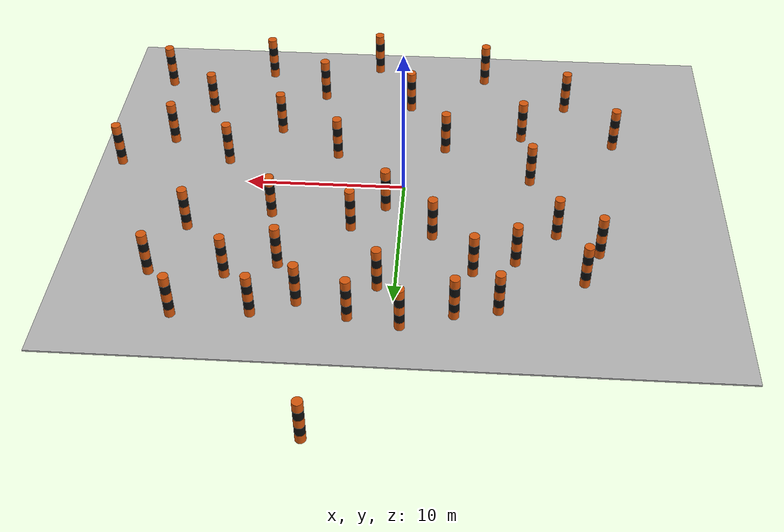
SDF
<?xml version='1.0'?>
<sdf version='1.6'>
  <world name='u_shape_lightweight'>

    <gui fullscreen='0'>
      <camera name='user_camera'>
        <pose>-49 27 52 0 0.75 -0.76 0</pose>
      </camera>
    </gui>

    <shadows>0</shadows>

    <light name='sun' type='directional'>
      <cast_shadows>0</cast_shadows>
      <pose>0 0 20 0 0 0</pose>
      <diffuse>0.8 0.8 0.8 1</diffuse>
      <specular>0.2 0.2 0.2 1</specular>

      <attenuation>
        <range>1000</range>
        <constant>0.9</constant>
        <linear>0.01</linear>
        <quadratic>0.001</quadratic>
      </attenuation>

      <direction>-0.5 0.1 -0.9</direction>
    </light>

    <physics name='default_physics' default='1' type='ode'>
      <max_step_size>0.005</max_step_size>
      <real_time_factor>1</real_time_factor>
      <real_time_update_rate>200</real_time_update_rate>
    </physics>

    <!-- Ground: cheap tiled texture, gives LK a feature-rich   -->
    <!-- ground plane at near-zero render cost.                 -->

    <model name='ground'>
      <static>true</static>
      <link name='link'>
        <collision name='collision'>
          <geometry>
            <box><size>40 30 0.1</size></box>
          </geometry>
        </collision>
        <visual name='visual'>
          <geometry>
            <box><size>40 30 0.1</size></box>
          </geometry>
        </visual>
      </link>
      <pose>0 0 -0.05 0 0 0</pose>
    </model>

    <!-- Striped-pole obstacles, fully inlined (no model://     -->
    <!-- include - that requires an installed model directory  -->
    <!-- and will NOT resolve to a model defined in this same    -->
    <!-- file). Each pole: one cheap cylinder collision +        -->
    <!-- 5 color-banded visual segments for LK-trackable corners.-->

    <!-- MEDIUM FOREST OBSTACLES -->

    <model name='pole_01'>
      <static>true</static>
      <pose>-12 5.5 0 0 0 0</pose>
      <link name='link'>
        <collision name='collision'>
          <pose>0 0 1.5 0 0 0</pose>
          <geometry>
            <cylinder>
              <radius>0.30</radius>
              <length>3.0</length>
            </cylinder>
          </geometry>
        </collision>

        <visual name='b1'>
          <pose>0 0 0.3 0 0 0</pose>
          <geometry><cylinder><radius>0.30</radius><length>0.6</length></cylinder></geometry>
          <material>
            <ambient>0.85 0.35 0.05 1</ambient>
            <diffuse>0.85 0.35 0.05 1</diffuse>
          </material>
        </visual>

        <visual name='b2'>
          <pose>0 0 0.9 0 0 0</pose>
          <geometry><cylinder><radius>0.30</radius><length>0.6</length></cylinder></geometry>
          <material>
            <ambient>0.05 0.05 0.05 1</ambient>
            <diffuse>0.05 0.05 0.05 1</diffuse>
          </material>
        </visual>

        <visual name='b3'>
          <pose>0 0 1.5 0 0 0</pose>
          <geometry><cylinder><radius>0.30</radius><length>0.6</length></cylinder></geometry>
          <material>
            <ambient>0.85 0.35 0.05 1</ambient>
            <diffuse>0.85 0.35 0.05 1</diffuse>
          </material>
        </visual>

        <visual name='b4'>
          <pose>0 0 2.1 0 0 0</pose>
          <geometry><cylinder><radius>0.30</radius><length>0.6</length></cylinder></geometry>
          <material>
            <ambient>0.05 0.05 0.05 1</ambient>
            <diffuse>0.05 0.05 0.05 1</diffuse>
          </material>
        </visual>

        <visual name='b5'>
          <pose>0 0 2.7 0 0 0</pose>
          <geometry><cylinder><radius>0.30</radius><length>0.6</length></cylinder></geometry>
          <material>
            <ambient>0.85 0.35 0.05 1</ambient>
            <diffuse>0.85 0.35 0.05 1</diffuse>
          </material>
        </visual>
      </link>
    </model>

    <model name='pole_02'>
      <static>true</static>
      <pose>-11 8 0 0 0 0</pose>
      <link name='link'>
        <collision name='collision'>
          <pose>0 0 1.5 0 0 0</pose>
          <geometry>
            <cylinder>
              <radius>0.30</radius>
              <length>3.0</length>
            </cylinder>
          </geometry>
        </collision>

        <visual name='b1'>
          <pose>0 0 0.3 0 0 0</pose>
          <geometry><cylinder><radius>0.30</radius><length>0.6</length></cylinder></geometry>
          <material>
            <ambient>0.85 0.35 0.05 1</ambient>
            <diffuse>0.85 0.35 0.05 1</diffuse>
          </material>
        </visual>

        <visual name='b2'>
          <pose>0 0 0.9 0 0 0</pose>
          <geometry><cylinder><radius>0.30</radius><length>0.6</length></cylinder></geometry>
          <material>
            <ambient>0.05 0.05 0.05 1</ambient>
            <diffuse>0.05 0.05 0.05 1</diffuse>
          </material>
        </visual>

        <visual name='b3'>
          <pose>0 0 1.5 0 0 0</pose>
          <geometry><cylinder><radius>0.30</radius><length>0.6</length></cylinder></geometry>
          <material>
            <ambient>0.85 0.35 0.05 1</ambient>
            <diffuse>0.85 0.35 0.05 1</diffuse>
          </material>
        </visual>

        <visual name='b4'>
          <pose>0 0 2.1 0 0 0</pose>
          <geometry><cylinder><radius>0.30</radius><length>0.6</length></cylinder></geometry>
          <material>
            <ambient>0.05 0.05 0.05 1</ambient>
            <diffuse>0.05 0.05 0.05 1</diffuse>
          </material>
        </visual>

        <visual name='b5'>
          <pose>0 0 2.7 0 0 0</pose>
          <geometry><cylinder><radius>0.30</radius><length>0.6</length></cylinder></geometry>
          <material>
            <ambient>0.85 0.35 0.05 1</ambient>
            <diffuse>0.85 0.35 0.05 1</diffuse>
          </material>
        </visual>
      </link>
    </model>

    <model name='pole_03'>
      <static>true</static>
      <pose>-9.5 4 0 0 0 0</pose>
      <link name='link'>
        <collision name='collision'>
          <pose>0 0 1.5 0 0 0</pose>
          <geometry>
            <cylinder>
              <radius>0.30</radius>
              <length>3.0</length>
            </cylinder>
          </geometry>
        </collision>

        <visual name='b1'>
          <pose>0 0 0.3 0 0 0</pose>
          <geometry><cylinder><radius>0.30</radius><length>0.6</length></cylinder></geometry>
          <material>
            <ambient>0.85 0.35 0.05 1</ambient>
            <diffuse>0.85 0.35 0.05 1</diffuse>
          </material>
        </visual>

        <visual name='b2'>
          <pose>0 0 0.9 0 0 0</pose>
          <geometry><cylinder><radius>0.30</radius><length>0.6</length></cylinder></geometry>
          <material>
            <ambient>0.05 0.05 0.05 1</ambient>
            <diffuse>0.05 0.05 0.05 1</diffuse>
          </material>
        </visual>

        <visual name='b3'>
          <pose>0 0 1.5 0 0 0</pose>
          <geometry><cylinder><radius>0.30</radius><length>0.6</length></cylinder></geometry>
          <material>
            <ambient>0.85 0.35 0.05 1</ambient>
            <diffuse>0.85 0.35 0.05 1</diffuse>
          </material>
        </visual>

        <visual name='b4'>
          <pose>0 0 2.1 0 0 0</pose>
          <geometry><cylinder><radius>0.30</radius><length>0.6</length></cylinder></geometry>
          <material>
            <ambient>0.05 0.05 0.05 1</ambient>
            <diffuse>0.05 0.05 0.05 1</diffuse>
          </material>
        </visual>

        <visual name='b5'>
          <pose>0 0 2.7 0 0 0</pose>
          <geometry><cylinder><radius>0.30</radius><length>0.6</length></cylinder></geometry>
          <material>
            <ambient>0.85 0.35 0.05 1</ambient>
            <diffuse>0.85 0.35 0.05 1</diffuse>
          </material>
        </visual>
      </link>
    </model>

    <model name='pole_04'>
      <static>true</static>
      <pose>1 2 0 0 0 0</pose>
      <link name='link'>
        <collision name='collision'>
          <pose>0 0 1.5 0 0 0</pose>
          <geometry>
            <cylinder>
              <radius>0.30</radius>
              <length>3.0</length>
            </cylinder>
          </geometry>
        </collision>

        <visual name='b1'>
          <pose>0 0 0.3 0 0 0</pose>
          <geometry><cylinder><radius>0.30</radius><length>0.6</length></cylinder></geometry>
          <material>
            <ambient>0.85 0.35 0.05 1</ambient>
            <diffuse>0.85 0.35 0.05 1</diffuse>
          </material>
        </visual>

        <visual name='b2'>
          <pose>0 0 0.9 0 0 0</pose>
          <geometry><cylinder><radius>0.30</radius><length>0.6</length></cylinder></geometry>
          <material>
            <ambient>0.05 0.05 0.05 1</ambient>
            <diffuse>0.05 0.05 0.05 1</diffuse>
          </material>
        </visual>

        <visual name='b3'>
          <pose>0 0 1.5 0 0 0</pose>
          <geometry><cylinder><radius>0.30</radius><length>0.6</length></cylinder></geometry>
          <material>
            <ambient>0.85 0.35 0.05 1</ambient>
            <diffuse>0.85 0.35 0.05 1</diffuse>
          </material>
        </visual>

        <visual name='b4'>
          <pose>0 0 2.1 0 0 0</pose>
          <geometry><cylinder><radius>0.30</radius><length>0.6</length></cylinder></geometry>
          <material>
            <ambient>0.05 0.05 0.05 1</ambient>
            <diffuse>0.05 0.05 0.05 1</diffuse>
          </material>
        </visual>

        <visual name='b5'>
          <pose>0 0 2.7 0 0 0</pose>
          <geometry><cylinder><radius>0.30</radius><length>0.6</length></cylinder></geometry>
          <material>
            <ambient>0.85 0.35 0.05 1</ambient>
            <diffuse>0.85 0.35 0.05 1</diffuse>
          </material>
        </visual>
      </link>
    </model>

    <model name='pole_05'>
      <static>true</static>
      <pose>-7 6.5 0 0 0 0</pose>
      <link name='link'>
        <collision name='collision'>
          <pose>0 0 1.5 0 0 0</pose>
          <geometry>
            <cylinder>
              <radius>0.30</radius>
              <length>3.0</length>
            </cylinder>
          </geometry>
        </collision>

        <visual name='b1'>
          <pose>0 0 0.3 0 0 0</pose>
          <geometry><cylinder><radius>0.30</radius><length>0.6</length></cylinder></geometry>
          <material>
            <ambient>0.85 0.35 0.05 1</ambient>
            <diffuse>0.85 0.35 0.05 1</diffuse>
          </material>
        </visual>

        <visual name='b2'>
          <pose>0 0 0.9 0 0 0</pose>
          <geometry><cylinder><radius>0.30</radius><length>0.6</length></cylinder></geometry>
          <material>
            <ambient>0.05 0.05 0.05 1</ambient>
            <diffuse>0.05 0.05 0.05 1</diffuse>
          </material>
        </visual>

        <visual name='b3'>
          <pose>0 0 1.5 0 0 0</pose>
          <geometry><cylinder><radius>0.30</radius><length>0.6</length></cylinder></geometry>
          <material>
            <ambient>0.85 0.35 0.05 1</ambient>
            <diffuse>0.85 0.35 0.05 1</diffuse>
          </material>
        </visual>

        <visual name='b4'>
          <pose>0 0 2.1 0 0 0</pose>
          <geometry><cylinder><radius>0.30</radius><length>0.6</length></cylinder></geometry>
          <material>
            <ambient>0.05 0.05 0.05 1</ambient>
            <diffuse>0.05 0.05 0.05 1</diffuse>
          </material>
        </visual>

        <visual name='b5'>
          <pose>0 0 2.7 0 0 0</pose>
          <geometry><cylinder><radius>0.30</radius><length>0.6</length></cylinder></geometry>
          <material>
            <ambient>0.85 0.35 0.05 1</ambient>
            <diffuse>0.85 0.35 0.05 1</diffuse>
          </material>
        </visual>
      </link>
    </model>

    <model name='pole_06'>
      <static>true</static>
      <pose>-6 10.5 0 0 0 0</pose>
      <link name='link'>
        <collision name='collision'>
          <pose>0 0 1.5 0 0 0</pose>
          <geometry>
            <cylinder>
              <radius>0.30</radius>
              <length>3.0</length>
            </cylinder>
          </geometry>
        </collision>

        <visual name='b1'>
          <pose>0 0 0.3 0 0 0</pose>
          <geometry><cylinder><radius>0.30</radius><length>0.6</length></cylinder></geometry>
          <material>
            <ambient>0.85 0.35 0.05 1</ambient>
            <diffuse>0.85 0.35 0.05 1</diffuse>
          </material>
        </visual>

        <visual name='b2'>
          <pose>0 0 0.9 0 0 0</pose>
          <geometry><cylinder><radius>0.30</radius><length>0.6</length></cylinder></geometry>
          <material>
            <ambient>0.05 0.05 0.05 1</ambient>
            <diffuse>0.05 0.05 0.05 1</diffuse>
          </material>
        </visual>

        <visual name='b3'>
          <pose>0 0 1.5 0 0 0</pose>
          <geometry><cylinder><radius>0.30</radius><length>0.6</length></cylinder></geometry>
          <material>
            <ambient>0.85 0.35 0.05 1</ambient>
            <diffuse>0.85 0.35 0.05 1</diffuse>
          </material>
        </visual>

        <visual name='b4'>
          <pose>0 0 2.1 0 0 0</pose>
          <geometry><cylinder><radius>0.30</radius><length>0.6</length></cylinder></geometry>
          <material>
            <ambient>0.05 0.05 0.05 1</ambient>
            <diffuse>0.05 0.05 0.05 1</diffuse>
          </material>
        </visual>

        <visual name='b5'>
          <pose>0 0 2.7 0 0 0</pose>
          <geometry><cylinder><radius>0.30</radius><length>0.6</length></cylinder></geometry>
          <material>
            <ambient>0.85 0.35 0.05 1</ambient>
            <diffuse>0.85 0.35 0.05 1</diffuse>
          </material>
        </visual>
      </link>
    </model>

    <model name='pole_07'>
      <static>true</static>
      <pose>-4.5 7.5 0 0 0 0</pose>
      <link name='link'>
        <collision name='collision'>
          <pose>0 0 1.5 0 0 0</pose>
          <geometry>
            <cylinder>
              <radius>0.30</radius>
              <length>3.0</length>
            </cylinder>
          </geometry>
        </collision>

        <visual name='b1'>
          <pose>0 0 0.3 0 0 0</pose>
          <geometry><cylinder><radius>0.30</radius><length>0.6</length></cylinder></geometry>
          <material>
            <ambient>0.85 0.35 0.05 1</ambient>
            <diffuse>0.85 0.35 0.05 1</diffuse>
          </material>
        </visual>

        <visual name='b2'>
          <pose>0 0 0.9 0 0 0</pose>
          <geometry><cylinder><radius>0.30</radius><length>0.6</length></cylinder></geometry>
          <material>
            <ambient>0.05 0.05 0.05 1</ambient>
            <diffuse>0.05 0.05 0.05 1</diffuse>
          </material>
        </visual>

        <visual name='b3'>
          <pose>0 0 1.5 0 0 0</pose>
          <geometry><cylinder><radius>0.30</radius><length>0.6</length></cylinder></geometry>
          <material>
            <ambient>0.85 0.35 0.05 1</ambient>
            <diffuse>0.85 0.35 0.05 1</diffuse>
          </material>
        </visual>

        <visual name='b4'>
          <pose>0 0 2.1 0 0 0</pose>
          <geometry><cylinder><radius>0.30</radius><length>0.6</length></cylinder></geometry>
          <material>
            <ambient>0.05 0.05 0.05 1</ambient>
            <diffuse>0.05 0.05 0.05 1</diffuse>
          </material>
        </visual>

        <visual name='b5'>
          <pose>0 0 2.7 0 0 0</pose>
          <geometry><cylinder><radius>0.30</radius><length>0.6</length></cylinder></geometry>
          <material>
            <ambient>0.85 0.35 0.05 1</ambient>
            <diffuse>0.85 0.35 0.05 1</diffuse>
          </material>
        </visual>
      </link>
    </model>

    <model name='pole_08'>
      <static>true</static>
      <pose>-3.5 11 0 0 0 0</pose>
      <link name='link'>
        <collision name='collision'>
          <pose>0 0 1.5 0 0 0</pose>
          <geometry>
            <cylinder>
              <radius>0.30</radius>
              <length>3.0</length>
            </cylinder>
          </geometry>
        </collision>

        <visual name='b1'>
          <pose>0 0 0.3 0 0 0</pose>
          <geometry><cylinder><radius>0.30</radius><length>0.6</length></cylinder></geometry>
          <material>
            <ambient>0.85 0.35 0.05 1</ambient>
            <diffuse>0.85 0.35 0.05 1</diffuse>
          </material>
        </visual>

        <visual name='b2'>
          <pose>0 0 0.9 0 0 0</pose>
          <geometry><cylinder><radius>0.30</radius><length>0.6</length></cylinder></geometry>
          <material>
            <ambient>0.05 0.05 0.05 1</ambient>
            <diffuse>0.05 0.05 0.05 1</diffuse>
          </material>
        </visual>

        <visual name='b3'>
          <pose>0 0 1.5 0 0 0</pose>
          <geometry><cylinder><radius>0.30</radius><length>0.6</length></cylinder></geometry>
          <material>
            <ambient>0.85 0.35 0.05 1</ambient>
            <diffuse>0.85 0.35 0.05 1</diffuse>
          </material>
        </visual>

        <visual name='b4'>
          <pose>0 0 2.1 0 0 0</pose>
          <geometry><cylinder><radius>0.30</radius><length>0.6</length></cylinder></geometry>
          <material>
            <ambient>0.05 0.05 0.05 1</ambient>
            <diffuse>0.05 0.05 0.05 1</diffuse>
          </material>
        </visual>

        <visual name='b5'>
          <pose>0 0 2.7 0 0 0</pose>
          <geometry><cylinder><radius>0.30</radius><length>0.6</length></cylinder></geometry>
          <material>
            <ambient>0.85 0.35 0.05 1</ambient>
            <diffuse>0.85 0.35 0.05 1</diffuse>
          </material>
        </visual>
      </link>
    </model>

    <model name='pole_09'>
      <static>true</static>
      <pose>-2 4.5 0 0 0 0</pose>
      <link name='link'>
        <collision name='collision'>
          <pose>0 0 1.5 0 0 0</pose>
          <geometry>
            <cylinder>
              <radius>0.30</radius>
              <length>3.0</length>
            </cylinder>
          </geometry>
        </collision>

        <visual name='b1'>
          <pose>0 0 0.3 0 0 0</pose>
          <geometry><cylinder><radius>0.30</radius><length>0.6</length></cylinder></geometry>
          <material>
            <ambient>0.85 0.35 0.05 1</ambient>
            <diffuse>0.85 0.35 0.05 1</diffuse>
          </material>
        </visual>

        <visual name='b2'>
          <pose>0 0 0.9 0 0 0</pose>
          <geometry><cylinder><radius>0.30</radius><length>0.6</length></cylinder></geometry>
          <material>
            <ambient>0.05 0.05 0.05 1</ambient>
            <diffuse>0.05 0.05 0.05 1</diffuse>
          </material>
        </visual>

        <visual name='b3'>
          <pose>0 0 1.5 0 0 0</pose>
          <geometry><cylinder><radius>0.30</radius><length>0.6</length></cylinder></geometry>
          <material>
            <ambient>0.85 0.35 0.05 1</ambient>
            <diffuse>0.85 0.35 0.05 1</diffuse>
          </material>
        </visual>

        <visual name='b4'>
          <pose>0 0 2.1 0 0 0</pose>
          <geometry><cylinder><radius>0.30</radius><length>0.6</length></cylinder></geometry>
          <material>
            <ambient>0.05 0.05 0.05 1</ambient>
            <diffuse>0.05 0.05 0.05 1</diffuse>
          </material>
        </visual>

        <visual name='b5'>
          <pose>0 0 2.7 0 0 0</pose>
          <geometry><cylinder><radius>0.30</radius><length>0.6</length></cylinder></geometry>
          <material>
            <ambient>0.85 0.35 0.05 1</ambient>
            <diffuse>0.85 0.35 0.05 1</diffuse>
          </material>
        </visual>
      </link>
    </model>

    <model name='pole_10'>
      <static>true</static>
      <pose>-0.5 12 0 0 0 0</pose>
      <link name='link'>
        <collision name='collision'>
          <pose>0 0 1.5 0 0 0</pose>
          <geometry>
            <cylinder>
              <radius>0.30</radius>
              <length>3.0</length>
            </cylinder>
          </geometry>
        </collision>

        <visual name='b1'>
          <pose>0 0 0.3 0 0 0</pose>
          <geometry><cylinder><radius>0.30</radius><length>0.6</length></cylinder></geometry>
          <material>
            <ambient>0.85 0.35 0.05 1</ambient>
            <diffuse>0.85 0.35 0.05 1</diffuse>
          </material>
        </visual>

        <visual name='b2'>
          <pose>0 0 0.9 0 0 0</pose>
          <geometry><cylinder><radius>0.30</radius><length>0.6</length></cylinder></geometry>
          <material>
            <ambient>0.05 0.05 0.05 1</ambient>
            <diffuse>0.05 0.05 0.05 1</diffuse>
          </material>
        </visual>

        <visual name='b3'>
          <pose>0 0 1.5 0 0 0</pose>
          <geometry><cylinder><radius>0.30</radius><length>0.6</length></cylinder></geometry>
          <material>
            <ambient>0.85 0.35 0.05 1</ambient>
            <diffuse>0.85 0.35 0.05 1</diffuse>
          </material>
        </visual>

        <visual name='b4'>
          <pose>0 0 2.1 0 0 0</pose>
          <geometry><cylinder><radius>0.30</radius><length>0.6</length></cylinder></geometry>
          <material>
            <ambient>0.05 0.05 0.05 1</ambient>
            <diffuse>0.05 0.05 0.05 1</diffuse>
          </material>
        </visual>

        <visual name='b5'>
          <pose>0 0 2.7 0 0 0</pose>
          <geometry><cylinder><radius>0.30</radius><length>0.6</length></cylinder></geometry>
          <material>
            <ambient>0.85 0.35 0.05 1</ambient>
            <diffuse>0.85 0.35 0.05 1</diffuse>
          </material>
        </visual>
      </link>
    </model>

    <model name='pole_11'>
      <static>true</static>
      <pose>1 9 0 0 0 0</pose>
      <link name='link'>
        <collision name='collision'>
          <pose>0 0 1.5 0 0 0</pose>
          <geometry>
            <cylinder>
              <radius>0.30</radius>
              <length>3.0</length>
            </cylinder>
          </geometry>
        </collision>

        <visual name='b1'>
          <pose>0 0 0.3 0 0 0</pose>
          <geometry><cylinder><radius>0.30</radius><length>0.6</length></cylinder></geometry>
          <material>
            <ambient>0.85 0.35 0.05 1</ambient>
            <diffuse>0.85 0.35 0.05 1</diffuse>
          </material>
        </visual>

        <visual name='b2'>
          <pose>0 0 0.9 0 0 0</pose>
          <geometry><cylinder><radius>0.30</radius><length>0.6</length></cylinder></geometry>
          <material>
            <ambient>0.05 0.05 0.05 1</ambient>
            <diffuse>0.05 0.05 0.05 1</diffuse>
          </material>
        </visual>

        <visual name='b3'>
          <pose>0 0 1.5 0 0 0</pose>
          <geometry><cylinder><radius>0.30</radius><length>0.6</length></cylinder></geometry>
          <material>
            <ambient>0.85 0.35 0.05 1</ambient>
            <diffuse>0.85 0.35 0.05 1</diffuse>
          </material>
        </visual>

        <visual name='b4'>
          <pose>0 0 2.1 0 0 0</pose>
          <geometry><cylinder><radius>0.30</radius><length>0.6</length></cylinder></geometry>
          <material>
            <ambient>0.05 0.05 0.05 1</ambient>
            <diffuse>0.05 0.05 0.05 1</diffuse>
          </material>
        </visual>

        <visual name='b5'>
          <pose>0 0 2.7 0 0 0</pose>
          <geometry><cylinder><radius>0.30</radius><length>0.6</length></cylinder></geometry>
          <material>
            <ambient>0.85 0.35 0.05 1</ambient>
            <diffuse>0.85 0.35 0.05 1</diffuse>
          </material>
        </visual>
      </link>
    </model>

    <model name='pole_12'>
      <static>true</static>
      <pose>2.5 11.5 0 0 0 0</pose>
      <link name='link'>
        <collision name='collision'>
          <pose>0 0 1.5 0 0 0</pose>
          <geometry>
            <cylinder>
              <radius>0.30</radius>
              <length>3.0</length>
            </cylinder>
          </geometry>
        </collision>

        <visual name='b1'>
          <pose>0 0 0.3 0 0 0</pose>
          <geometry><cylinder><radius>0.30</radius><length>0.6</length></cylinder></geometry>
          <material>
            <ambient>0.85 0.35 0.05 1</ambient>
            <diffuse>0.85 0.35 0.05 1</diffuse>
          </material>
        </visual>

        <visual name='b2'>
          <pose>0 0 0.9 0 0 0</pose>
          <geometry><cylinder><radius>0.30</radius><length>0.6</length></cylinder></geometry>
          <material>
            <ambient>0.05 0.05 0.05 1</ambient>
            <diffuse>0.05 0.05 0.05 1</diffuse>
          </material>
        </visual>

        <visual name='b3'>
          <pose>0 0 1.5 0 0 0</pose>
          <geometry><cylinder><radius>0.30</radius><length>0.6</length></cylinder></geometry>
          <material>
            <ambient>0.85 0.35 0.05 1</ambient>
            <diffuse>0.85 0.35 0.05 1</diffuse>
          </material>
        </visual>

        <visual name='b4'>
          <pose>0 0 2.1 0 0 0</pose>
          <geometry><cylinder><radius>0.30</radius><length>0.6</length></cylinder></geometry>
          <material>
            <ambient>0.05 0.05 0.05 1</ambient>
            <diffuse>0.05 0.05 0.05 1</diffuse>
          </material>
        </visual>

        <visual name='b5'>
          <pose>0 0 2.7 0 0 0</pose>
          <geometry><cylinder><radius>0.30</radius><length>0.6</length></cylinder></geometry>
          <material>
            <ambient>0.85 0.35 0.05 1</ambient>
            <diffuse>0.85 0.35 0.05 1</diffuse>
          </material>
        </visual>
      </link>
    </model>

    <model name='pole_13'>
      <static>true</static>
      <pose>4 20 0 0 0 0</pose>
      <link name='link'>
        <collision name='collision'>
          <pose>0 0 1.5 0 0 0</pose>
          <geometry>
            <cylinder>
              <radius>0.30</radius>
              <length>3.0</length>
            </cylinder>
          </geometry>
        </collision>

        <visual name='b1'>
          <pose>0 0 0.3 0 0 0</pose>
          <geometry><cylinder><radius>0.30</radius><length>0.6</length></cylinder></geometry>
          <material>
            <ambient>0.85 0.35 0.05 1</ambient>
            <diffuse>0.85 0.35 0.05 1</diffuse>
          </material>
        </visual>

        <visual name='b2'>
          <pose>0 0 0.9 0 0 0</pose>
          <geometry><cylinder><radius>0.30</radius><length>0.6</length></cylinder></geometry>
          <material>
            <ambient>0.05 0.05 0.05 1</ambient>
            <diffuse>0.05 0.05 0.05 1</diffuse>
          </material>
        </visual>

        <visual name='b3'>
          <pose>0 0 1.5 0 0 0</pose>
          <geometry><cylinder><radius>0.30</radius><length>0.6</length></cylinder></geometry>
          <material>
            <ambient>0.85 0.35 0.05 1</ambient>
            <diffuse>0.85 0.35 0.05 1</diffuse>
          </material>
        </visual>

        <visual name='b4'>
          <pose>0 0 2.1 0 0 0</pose>
          <geometry><cylinder><radius>0.30</radius><length>0.6</length></cylinder></geometry>
          <material>
            <ambient>0.05 0.05 0.05 1</ambient>
            <diffuse>0.05 0.05 0.05 1</diffuse>
          </material>
        </visual>

        <visual name='b5'>
          <pose>0 0 2.7 0 0 0</pose>
          <geometry><cylinder><radius>0.30</radius><length>0.6</length></cylinder></geometry>
          <material>
            <ambient>0.85 0.35 0.05 1</ambient>
            <diffuse>0.85 0.35 0.05 1</diffuse>
          </material>
        </visual>
      </link>
    </model>

    <model name='pole_14'>
      <static>true</static>
      <pose>5.5 10.5 0 0 0 0</pose>
      <link name='link'>
        <collision name='collision'>
          <pose>0 0 1.5 0 0 0</pose>
          <geometry>
            <cylinder>
              <radius>0.30</radius>
              <length>3.0</length>
            </cylinder>
          </geometry>
        </collision>

        <visual name='b1'>
          <pose>0 0 0.3 0 0 0</pose>
          <geometry><cylinder><radius>0.30</radius><length>0.6</length></cylinder></geometry>
          <material>
            <ambient>0.85 0.35 0.05 1</ambient>
            <diffuse>0.85 0.35 0.05 1</diffuse>
          </material>
        </visual>

        <visual name='b2'>
          <pose>0 0 0.9 0 0 0</pose>
          <geometry><cylinder><radius>0.30</radius><length>0.6</length></cylinder></geometry>
          <material>
            <ambient>0.05 0.05 0.05 1</ambient>
            <diffuse>0.05 0.05 0.05 1</diffuse>
          </material>
        </visual>

        <visual name='b3'>
          <pose>0 0 1.5 0 0 0</pose>
          <geometry><cylinder><radius>0.30</radius><length>0.6</length></cylinder></geometry>
          <material>
            <ambient>0.85 0.35 0.05 1</ambient>
            <diffuse>0.85 0.35 0.05 1</diffuse>
          </material>
        </visual>

        <visual name='b4'>
          <pose>0 0 2.1 0 0 0</pose>
          <geometry><cylinder><radius>0.30</radius><length>0.6</length></cylinder></geometry>
          <material>
            <ambient>0.05 0.05 0.05 1</ambient>
            <diffuse>0.05 0.05 0.05 1</diffuse>
          </material>
        </visual>

        <visual name='b5'>
          <pose>0 0 2.7 0 0 0</pose>
          <geometry><cylinder><radius>0.30</radius><length>0.6</length></cylinder></geometry>
          <material>
            <ambient>0.85 0.35 0.05 1</ambient>
            <diffuse>0.85 0.35 0.05 1</diffuse>
          </material>
        </visual>
      </link>
    </model>

    <model name='pole_15'>
      <static>true</static>
      <pose>7 7.5 0 0 0 0</pose>
      <link name='link'>
        <collision name='collision'>
          <pose>0 0 1.5 0 0 0</pose>
          <geometry>
            <cylinder>
              <radius>0.30</radius>
              <length>3.0</length>
            </cylinder>
          </geometry>
        </collision>

        <visual name='b1'>
          <pose>0 0 0.3 0 0 0</pose>
          <geometry><cylinder><radius>0.30</radius><length>0.6</length></cylinder></geometry>
          <material>
            <ambient>0.85 0.35 0.05 1</ambient>
            <diffuse>0.85 0.35 0.05 1</diffuse>
          </material>
        </visual>

        <visual name='b2'>
          <pose>0 0 0.9 0 0 0</pose>
          <geometry><cylinder><radius>0.30</radius><length>0.6</length></cylinder></geometry>
          <material>
            <ambient>0.05 0.05 0.05 1</ambient>
            <diffuse>0.05 0.05 0.05 1</diffuse>
          </material>
        </visual>

        <visual name='b3'>
          <pose>0 0 1.5 0 0 0</pose>
          <geometry><cylinder><radius>0.30</radius><length>0.6</length></cylinder></geometry>
          <material>
            <ambient>0.85 0.35 0.05 1</ambient>
            <diffuse>0.85 0.35 0.05 1</diffuse>
          </material>
        </visual>

        <visual name='b4'>
          <pose>0 0 2.1 0 0 0</pose>
          <geometry><cylinder><radius>0.30</radius><length>0.6</length></cylinder></geometry>
          <material>
            <ambient>0.05 0.05 0.05 1</ambient>
            <diffuse>0.05 0.05 0.05 1</diffuse>
          </material>
        </visual>

        <visual name='b5'>
          <pose>0 0 2.7 0 0 0</pose>
          <geometry><cylinder><radius>0.30</radius><length>0.6</length></cylinder></geometry>
          <material>
            <ambient>0.85 0.35 0.05 1</ambient>
            <diffuse>0.85 0.35 0.05 1</diffuse>
          </material>
        </visual>
      </link>
    </model>

    <model name='pole_16'>
      <static>true</static>
      <pose>8 11.5 0 0 0 0</pose>
      <link name='link'>
        <collision name='collision'>
          <pose>0 0 1.5 0 0 0</pose>
          <geometry>
            <cylinder>
              <radius>0.30</radius>
              <length>3.0</length>
            </cylinder>
          </geometry>
        </collision>

        <visual name='b1'>
          <pose>0 0 0.3 0 0 0</pose>
          <geometry><cylinder><radius>0.30</radius><length>0.6</length></cylinder></geometry>
          <material>
            <ambient>0.85 0.35 0.05 1</ambient>
            <diffuse>0.85 0.35 0.05 1</diffuse>
          </material>
        </visual>

        <visual name='b2'>
          <pose>0 0 0.9 0 0 0</pose>
          <geometry><cylinder><radius>0.30</radius><length>0.6</length></cylinder></geometry>
          <material>
            <ambient>0.05 0.05 0.05 1</ambient>
            <diffuse>0.05 0.05 0.05 1</diffuse>
          </material>
        </visual>

        <visual name='b3'>
          <pose>0 0 1.5 0 0 0</pose>
          <geometry><cylinder><radius>0.30</radius><length>0.6</length></cylinder></geometry>
          <material>
            <ambient>0.85 0.35 0.05 1</ambient>
            <diffuse>0.85 0.35 0.05 1</diffuse>
          </material>
        </visual>

        <visual name='b4'>
          <pose>0 0 2.1 0 0 0</pose>
          <geometry><cylinder><radius>0.30</radius><length>0.6</length></cylinder></geometry>
          <material>
            <ambient>0.05 0.05 0.05 1</ambient>
            <diffuse>0.05 0.05 0.05 1</diffuse>
          </material>
        </visual>

        <visual name='b5'>
          <pose>0 0 2.7 0 0 0</pose>
          <geometry><cylinder><radius>0.30</radius><length>0.6</length></cylinder></geometry>
          <material>
            <ambient>0.85 0.35 0.05 1</ambient>
            <diffuse>0.85 0.35 0.05 1</diffuse>
          </material>
        </visual>
      </link>
    </model>

    <model name='pole_17'>
      <static>true</static>
      <pose>10 8.5 0 0 0 0</pose>
      <link name='link'>
        <collision name='collision'>
          <pose>0 0 1.5 0 0 0</pose>
          <geometry>
            <cylinder>
              <radius>0.30</radius>
              <length>3.0</length>
            </cylinder>
          </geometry>
        </collision>

        <visual name='b1'>
          <pose>0 0 0.3 0 0 0</pose>
          <geometry><cylinder><radius>0.30</radius><length>0.6</length></cylinder></geometry>
          <material>
            <ambient>0.85 0.35 0.05 1</ambient>
            <diffuse>0.85 0.35 0.05 1</diffuse>
          </material>
        </visual>

        <visual name='b2'>
          <pose>0 0 0.9 0 0 0</pose>
          <geometry><cylinder><radius>0.30</radius><length>0.6</length></cylinder></geometry>
          <material>
            <ambient>0.05 0.05 0.05 1</ambient>
            <diffuse>0.05 0.05 0.05 1</diffuse>
          </material>
        </visual>

        <visual name='b3'>
          <pose>0 0 1.5 0 0 0</pose>
          <geometry><cylinder><radius>0.30</radius><length>0.6</length></cylinder></geometry>
          <material>
            <ambient>0.85 0.35 0.05 1</ambient>
            <diffuse>0.85 0.35 0.05 1</diffuse>
          </material>
        </visual>

        <visual name='b4'>
          <pose>0 0 2.1 0 0 0</pose>
          <geometry><cylinder><radius>0.30</radius><length>0.6</length></cylinder></geometry>
          <material>
            <ambient>0.05 0.05 0.05 1</ambient>
            <diffuse>0.05 0.05 0.05 1</diffuse>
          </material>
        </visual>

        <visual name='b5'>
          <pose>0 0 2.7 0 0 0</pose>
          <geometry><cylinder><radius>0.30</radius><length>0.6</length></cylinder></geometry>
          <material>
            <ambient>0.85 0.35 0.05 1</ambient>
            <diffuse>0.85 0.35 0.05 1</diffuse>
          </material>
        </visual>
      </link>
    </model>

    <model name='pole_19'>
      <static>true</static>
      <pose>12.5 11.8 0 0 0 0</pose>
      <link name='link'>
        <collision name='collision'>
          <pose>0 0 1.5 0 0 0</pose>
          <geometry>
            <cylinder>
              <radius>0.30</radius>
              <length>3.0</length>
            </cylinder>
          </geometry>
        </collision>

        <visual name='b1'>
          <pose>0 0 0.3 0 0 0</pose>
          <geometry><cylinder><radius>0.30</radius><length>0.6</length></cylinder></geometry>
          <material>
            <ambient>0.85 0.35 0.05 1</ambient>
            <diffuse>0.85 0.35 0.05 1</diffuse>
          </material>
        </visual>

        <visual name='b2'>
          <pose>0 0 0.9 0 0 0</pose>
          <geometry><cylinder><radius>0.30</radius><length>0.6</length></cylinder></geometry>
          <material>
            <ambient>0.05 0.05 0.05 1</ambient>
            <diffuse>0.05 0.05 0.05 1</diffuse>
          </material>
        </visual>

        <visual name='b3'>
          <pose>0 0 1.5 0 0 0</pose>
          <geometry><cylinder><radius>0.30</radius><length>0.6</length></cylinder></geometry>
          <material>
            <ambient>0.85 0.35 0.05 1</ambient>
            <diffuse>0.85 0.35 0.05 1</diffuse>
          </material>
        </visual>

        <visual name='b4'>
          <pose>0 0 2.1 0 0 0</pose>
          <geometry><cylinder><radius>0.30</radius><length>0.6</length></cylinder></geometry>
          <material>
            <ambient>0.05 0.05 0.05 1</ambient>
            <diffuse>0.05 0.05 0.05 1</diffuse>
          </material>
        </visual>

        <visual name='b5'>
          <pose>0 0 2.7 0 0 0</pose>
          <geometry><cylinder><radius>0.30</radius><length>0.6</length></cylinder></geometry>
          <material>
            <ambient>0.85 0.35 0.05 1</ambient>
            <diffuse>0.85 0.35 0.05 1</diffuse>
          </material>
        </visual>
      </link>
    </model>

    <model name='pole_20'>
      <static>true</static>
      <pose>14.5 8.5 0 0 0 0</pose>
      <link name='link'>
        <collision name='collision'>
          <pose>0 0 1.5 0 0 0</pose>
          <geometry>
            <cylinder>
              <radius>0.30</radius>
              <length>3.0</length>
            </cylinder>
          </geometry>
        </collision>

        <visual name='b1'>
          <pose>0 0 0.3 0 0 0</pose>
          <geometry><cylinder><radius>0.30</radius><length>0.6</length></cylinder></geometry>
          <material>
            <ambient>0.85 0.35 0.05 1</ambient>
            <diffuse>0.85 0.35 0.05 1</diffuse>
          </material>
        </visual>

        <visual name='b2'>
          <pose>0 0 0.9 0 0 0</pose>
          <geometry><cylinder><radius>0.30</radius><length>0.6</length></cylinder></geometry>
          <material>
            <ambient>0.05 0.05 0.05 1</ambient>
            <diffuse>0.05 0.05 0.05 1</diffuse>
          </material>
        </visual>

        <visual name='b3'>
          <pose>0 0 1.5 0 0 0</pose>
          <geometry><cylinder><radius>0.30</radius><length>0.6</length></cylinder></geometry>
          <material>
            <ambient>0.85 0.35 0.05 1</ambient>
            <diffuse>0.85 0.35 0.05 1</diffuse>
          </material>
        </visual>

        <visual name='b4'>
          <pose>0 0 2.1 0 0 0</pose>
          <geometry><cylinder><radius>0.30</radius><length>0.6</length></cylinder></geometry>
          <material>
            <ambient>0.05 0.05 0.05 1</ambient>
            <diffuse>0.05 0.05 0.05 1</diffuse>
          </material>
        </visual>

        <visual name='b5'>
          <pose>0 0 2.7 0 0 0</pose>
          <geometry><cylinder><radius>0.30</radius><length>0.6</length></cylinder></geometry>
          <material>
            <ambient>0.85 0.35 0.05 1</ambient>
            <diffuse>0.85 0.35 0.05 1</diffuse>
          </material>
        </visual>
      </link>
    </model>

    <model name='pole_21'>
      <static>true</static>
      <pose>-8 -1 0 0 0 0</pose>
      <link name='link'>
        <collision name='collision'>
          <pose>0 0 1.5 0 0 0</pose>
          <geometry>
            <cylinder>
              <radius>0.30</radius>
              <length>3.0</length>
            </cylinder>
          </geometry>
        </collision>

        <visual name='b1'>
          <pose>0 0 0.3 0 0 0</pose>
          <geometry><cylinder><radius>0.30</radius><length>0.6</length></cylinder></geometry>
          <material>
            <ambient>0.85 0.35 0.05 1</ambient>
            <diffuse>0.85 0.35 0.05 1</diffuse>
          </material>
        </visual>

        <visual name='b2'>
          <pose>0 0 0.9 0 0 0</pose>
          <geometry><cylinder><radius>0.30</radius><length>0.6</length></cylinder></geometry>
          <material>
            <ambient>0.05 0.05 0.05 1</ambient>
            <diffuse>0.05 0.05 0.05 1</diffuse>
          </material>
        </visual>

        <visual name='b3'>
          <pose>0 0 1.5 0 0 0</pose>
          <geometry><cylinder><radius>0.30</radius><length>0.6</length></cylinder></geometry>
          <material>
            <ambient>0.85 0.35 0.05 1</ambient>
            <diffuse>0.85 0.35 0.05 1</diffuse>
          </material>
        </visual>

        <visual name='b4'>
          <pose>0 0 2.1 0 0 0</pose>
          <geometry><cylinder><radius>0.30</radius><length>0.6</length></cylinder></geometry>
          <material>
            <ambient>0.05 0.05 0.05 1</ambient>
            <diffuse>0.05 0.05 0.05 1</diffuse>
          </material>
        </visual>

        <visual name='b5'>
          <pose>0 0 2.7 0 0 0</pose>
          <geometry><cylinder><radius>0.30</radius><length>0.6</length></cylinder></geometry>
          <material>
            <ambient>0.85 0.35 0.05 1</ambient>
            <diffuse>0.85 0.35 0.05 1</diffuse>
          </material>
        </visual>
      </link>
    </model>

    <model name='pole_22'>
      <static>true</static>
      <pose>3 4 0 0 0 0</pose>
      <link name='link'>
        <collision name='collision'>
          <pose>0 0 1.5 0 0 0</pose>
          <geometry>
            <cylinder>
              <radius>0.30</radius>
              <length>3.0</length>
            </cylinder>
          </geometry>
        </collision>

        <visual name='b1'>
          <pose>0 0 0.3 0 0 0</pose>
          <geometry><cylinder><radius>0.30</radius><length>0.6</length></cylinder></geometry>
          <material>
            <ambient>0.85 0.35 0.05 1</ambient>
            <diffuse>0.85 0.35 0.05 1</diffuse>
          </material>
        </visual>

        <visual name='b2'>
          <pose>0 0 0.9 0 0 0</pose>
          <geometry><cylinder><radius>0.30</radius><length>0.6</length></cylinder></geometry>
          <material>
            <ambient>0.05 0.05 0.05 1</ambient>
            <diffuse>0.05 0.05 0.05 1</diffuse>
          </material>
        </visual>

        <visual name='b3'>
          <pose>0 0 1.5 0 0 0</pose>
          <geometry><cylinder><radius>0.30</radius><length>0.6</length></cylinder></geometry>
          <material>
            <ambient>0.85 0.35 0.05 1</ambient>
            <diffuse>0.85 0.35 0.05 1</diffuse>
          </material>
        </visual>

        <visual name='b4'>
          <pose>0 0 2.1 0 0 0</pose>
          <geometry><cylinder><radius>0.30</radius><length>0.6</length></cylinder></geometry>
          <material>
            <ambient>0.05 0.05 0.05 1</ambient>
            <diffuse>0.05 0.05 0.05 1</diffuse>
          </material>
        </visual>

        <visual name='b5'>
          <pose>0 0 2.7 0 0 0</pose>
          <geometry><cylinder><radius>0.30</radius><length>0.6</length></cylinder></geometry>
          <material>
            <ambient>0.85 0.35 0.05 1</ambient>
            <diffuse>0.85 0.35 0.05 1</diffuse>
          </material>
        </visual>
      </link>
    </model>

    <model name='pole_23'>
      <static>true</static>
      <pose>8 3 0 0 0 0</pose>
      <link name='link'>
        <collision name='collision'>
          <pose>0 0 1.5 0 0 0</pose>
          <geometry>
            <cylinder>
              <radius>0.30</radius>
              <length>3.0</length>
            </cylinder>
          </geometry>
        </collision>

        <visual name='b1'>
          <pose>0 0 0.3 0 0 0</pose>
          <geometry><cylinder><radius>0.30</radius><length>0.6</length></cylinder></geometry>
          <material>
            <ambient>0.85 0.35 0.05 1</ambient>
            <diffuse>0.85 0.35 0.05 1</diffuse>
          </material>
        </visual>

        <visual name='b2'>
          <pose>0 0 0.9 0 0 0</pose>
          <geometry><cylinder><radius>0.30</radius><length>0.6</length></cylinder></geometry>
          <material>
            <ambient>0.05 0.05 0.05 1</ambient>
            <diffuse>0.05 0.05 0.05 1</diffuse>
          </material>
        </visual>

        <visual name='b3'>
          <pose>0 0 1.5 0 0 0</pose>
          <geometry><cylinder><radius>0.30</radius><length>0.6</length></cylinder></geometry>
          <material>
            <ambient>0.85 0.35 0.05 1</ambient>
            <diffuse>0.85 0.35 0.05 1</diffuse>
          </material>
        </visual>

        <visual name='b4'>
          <pose>0 0 2.1 0 0 0</pose>
          <geometry><cylinder><radius>0.30</radius><length>0.6</length></cylinder></geometry>
          <material>
            <ambient>0.05 0.05 0.05 1</ambient>
            <diffuse>0.05 0.05 0.05 1</diffuse>
          </material>
        </visual>

        <visual name='b5'>
          <pose>0 0 2.7 0 0 0</pose>
          <geometry><cylinder><radius>0.30</radius><length>0.6</length></cylinder></geometry>
          <material>
            <ambient>0.85 0.35 0.05 1</ambient>
            <diffuse>0.85 0.35 0.05 1</diffuse>
          </material>
        </visual>
      </link>
    </model>

    <model name='pole_24'>
      <static>true</static>
      <pose>13 4.5 0 0 0 0</pose>
      <link name='link'>
        <collision name='collision'>
          <pose>0 0 1.5 0 0 0</pose>
          <geometry>
            <cylinder>
              <radius>0.30</radius>
              <length>3.0</length>
            </cylinder>
          </geometry>
        </collision>

        <visual name='b1'>
          <pose>0 0 0.3 0 0 0</pose>
          <geometry><cylinder><radius>0.30</radius><length>0.6</length></cylinder></geometry>
          <material>
            <ambient>0.85 0.35 0.05 1</ambient>
            <diffuse>0.85 0.35 0.05 1</diffuse>
          </material>
        </visual>

        <visual name='b2'>
          <pose>0 0 0.9 0 0 0</pose>
          <geometry><cylinder><radius>0.30</radius><length>0.6</length></cylinder></geometry>
          <material>
            <ambient>0.05 0.05 0.05 1</ambient>
            <diffuse>0.05 0.05 0.05 1</diffuse>
          </material>
        </visual>

        <visual name='b3'>
          <pose>0 0 1.5 0 0 0</pose>
          <geometry><cylinder><radius>0.30</radius><length>0.6</length></cylinder></geometry>
          <material>
            <ambient>0.85 0.35 0.05 1</ambient>
            <diffuse>0.85 0.35 0.05 1</diffuse>
          </material>
        </visual>

        <visual name='b4'>
          <pose>0 0 2.1 0 0 0</pose>
          <geometry><cylinder><radius>0.30</radius><length>0.6</length></cylinder></geometry>
          <material>
            <ambient>0.05 0.05 0.05 1</ambient>
            <diffuse>0.05 0.05 0.05 1</diffuse>
          </material>
        </visual>

        <visual name='b5'>
          <pose>0 0 2.7 0 0 0</pose>
          <geometry><cylinder><radius>0.30</radius><length>0.6</length></cylinder></geometry>
          <material>
            <ambient>0.85 0.35 0.05 1</ambient>
            <diffuse>0.85 0.35 0.05 1</diffuse>
          </material>
        </visual>
      </link>
    </model>

    <!-- BALANCED RIGHT-HALF MEDIUM FOREST OBSTACLES -->

    <model name='pole_25'>
      <static>true</static>
      <pose>-13.5 -5 0 0 0 0</pose>
      <link name='link'>
        <collision name='collision'>
          <pose>0 0 1.5 0 0 0</pose>
          <geometry>
            <cylinder>
              <radius>0.30</radius>
              <length>3.0</length>
            </cylinder>
          </geometry>
        </collision>

        <visual name='b1'>
          <pose>0 0 0.3 0 0 0</pose>
          <geometry><cylinder><radius>0.30</radius><length>0.6</length></cylinder></geometry>
          <material>
            <ambient>0.85 0.35 0.05 1</ambient>
            <diffuse>0.85 0.35 0.05 1</diffuse>
          </material>
        </visual>

        <visual name='b2'>
          <pose>0 0 0.9 0 0 0</pose>
          <geometry><cylinder><radius>0.30</radius><length>0.6</length></cylinder></geometry>
          <material>
            <ambient>0.05 0.05 0.05 1</ambient>
            <diffuse>0.05 0.05 0.05 1</diffuse>
          </material>
        </visual>

        <visual name='b3'>
          <pose>0 0 1.5 0 0 0</pose>
          <geometry><cylinder><radius>0.30</radius><length>0.6</length></cylinder></geometry>
          <material>
            <ambient>0.85 0.35 0.05 1</ambient>
            <diffuse>0.85 0.35 0.05 1</diffuse>
          </material>
        </visual>

        <visual name='b4'>
          <pose>0 0 2.1 0 0 0</pose>
          <geometry><cylinder><radius>0.30</radius><length>0.6</length></cylinder></geometry>
          <material>
            <ambient>0.05 0.05 0.05 1</ambient>
            <diffuse>0.05 0.05 0.05 1</diffuse>
          </material>
        </visual>

        <visual name='b5'>
          <pose>0 0 2.7 0 0 0</pose>
          <geometry><cylinder><radius>0.30</radius><length>0.6</length></cylinder></geometry>
          <material>
            <ambient>0.85 0.35 0.05 1</ambient>
            <diffuse>0.85 0.35 0.05 1</diffuse>
          </material>
        </visual>
      </link>
    </model>

    <model name='pole_26'>
      <static>true</static>
      <pose>-10.5 -9 0 0 0 0</pose>
      <link name='link'>
        <collision name='collision'>
          <pose>0 0 1.5 0 0 0</pose>
          <geometry>
            <cylinder>
              <radius>0.30</radius>
              <length>3.0</length>
            </cylinder>
          </geometry>
        </collision>

        <visual name='b1'>
          <pose>0 0 0.3 0 0 0</pose>
          <geometry><cylinder><radius>0.30</radius><length>0.6</length></cylinder></geometry>
          <material>
            <ambient>0.85 0.35 0.05 1</ambient>
            <diffuse>0.85 0.35 0.05 1</diffuse>
          </material>
        </visual>

        <visual name='b2'>
          <pose>0 0 0.9 0 0 0</pose>
          <geometry><cylinder><radius>0.30</radius><length>0.6</length></cylinder></geometry>
          <material>
            <ambient>0.05 0.05 0.05 1</ambient>
            <diffuse>0.05 0.05 0.05 1</diffuse>
          </material>
        </visual>

        <visual name='b3'>
          <pose>0 0 1.5 0 0 0</pose>
          <geometry><cylinder><radius>0.30</radius><length>0.6</length></cylinder></geometry>
          <material>
            <ambient>0.85 0.35 0.05 1</ambient>
            <diffuse>0.85 0.35 0.05 1</diffuse>
          </material>
        </visual>

        <visual name='b4'>
          <pose>0 0 2.1 0 0 0</pose>
          <geometry><cylinder><radius>0.30</radius><length>0.6</length></cylinder></geometry>
          <material>
            <ambient>0.05 0.05 0.05 1</ambient>
            <diffuse>0.05 0.05 0.05 1</diffuse>
          </material>
        </visual>

        <visual name='b5'>
          <pose>0 0 2.7 0 0 0</pose>
          <geometry><cylinder><radius>0.30</radius><length>0.6</length></cylinder></geometry>
          <material>
            <ambient>0.85 0.35 0.05 1</ambient>
            <diffuse>0.85 0.35 0.05 1</diffuse>
          </material>
        </visual>
      </link>
    </model>

    <model name='pole_27'>
      <static>true</static>
      <pose>-7.5 -5.5 0 0 0 0</pose>
      <link name='link'>
        <collision name='collision'>
          <pose>0 0 1.5 0 0 0</pose>
          <geometry>
            <cylinder>
              <radius>0.30</radius>
              <length>3.0</length>
            </cylinder>
          </geometry>
        </collision>

        <visual name='b1'>
          <pose>0 0 0.3 0 0 0</pose>
          <geometry><cylinder><radius>0.30</radius><length>0.6</length></cylinder></geometry>
          <material>
            <ambient>0.85 0.35 0.05 1</ambient>
            <diffuse>0.85 0.35 0.05 1</diffuse>
          </material>
        </visual>

        <visual name='b2'>
          <pose>0 0 0.9 0 0 0</pose>
          <geometry><cylinder><radius>0.30</radius><length>0.6</length></cylinder></geometry>
          <material>
            <ambient>0.05 0.05 0.05 1</ambient>
            <diffuse>0.05 0.05 0.05 1</diffuse>
          </material>
        </visual>

        <visual name='b3'>
          <pose>0 0 1.5 0 0 0</pose>
          <geometry><cylinder><radius>0.30</radius><length>0.6</length></cylinder></geometry>
          <material>
            <ambient>0.85 0.35 0.05 1</ambient>
            <diffuse>0.85 0.35 0.05 1</diffuse>
          </material>
        </visual>

        <visual name='b4'>
          <pose>0 0 2.1 0 0 0</pose>
          <geometry><cylinder><radius>0.30</radius><length>0.6</length></cylinder></geometry>
          <material>
            <ambient>0.05 0.05 0.05 1</ambient>
            <diffuse>0.05 0.05 0.05 1</diffuse>
          </material>
        </visual>

        <visual name='b5'>
          <pose>0 0 2.7 0 0 0</pose>
          <geometry><cylinder><radius>0.30</radius><length>0.6</length></cylinder></geometry>
          <material>
            <ambient>0.85 0.35 0.05 1</ambient>
            <diffuse>0.85 0.35 0.05 1</diffuse>
          </material>
        </visual>
      </link>
    </model>

    <model name='pole_28'>
      <static>true</static>
      <pose>-5 -12 0 0 0 0</pose>
      <link name='link'>
        <collision name='collision'>
          <pose>0 0 1.5 0 0 0</pose>
          <geometry>
            <cylinder>
              <radius>0.30</radius>
              <length>3.0</length>
            </cylinder>
          </geometry>
        </collision>

        <visual name='b1'>
          <pose>0 0 0.3 0 0 0</pose>
          <geometry><cylinder><radius>0.30</radius><length>0.6</length></cylinder></geometry>
          <material>
            <ambient>0.85 0.35 0.05 1</ambient>
            <diffuse>0.85 0.35 0.05 1</diffuse>
          </material>
        </visual>

        <visual name='b2'>
          <pose>0 0 0.9 0 0 0</pose>
          <geometry><cylinder><radius>0.30</radius><length>0.6</length></cylinder></geometry>
          <material>
            <ambient>0.05 0.05 0.05 1</ambient>
            <diffuse>0.05 0.05 0.05 1</diffuse>
          </material>
        </visual>

        <visual name='b3'>
          <pose>0 0 1.5 0 0 0</pose>
          <geometry><cylinder><radius>0.30</radius><length>0.6</length></cylinder></geometry>
          <material>
            <ambient>0.85 0.35 0.05 1</ambient>
            <diffuse>0.85 0.35 0.05 1</diffuse>
          </material>
        </visual>

        <visual name='b4'>
          <pose>0 0 2.1 0 0 0</pose>
          <geometry><cylinder><radius>0.30</radius><length>0.6</length></cylinder></geometry>
          <material>
            <ambient>0.05 0.05 0.05 1</ambient>
            <diffuse>0.05 0.05 0.05 1</diffuse>
          </material>
        </visual>

        <visual name='b5'>
          <pose>0 0 2.7 0 0 0</pose>
          <geometry><cylinder><radius>0.30</radius><length>0.6</length></cylinder></geometry>
          <material>
            <ambient>0.85 0.35 0.05 1</ambient>
            <diffuse>0.85 0.35 0.05 1</diffuse>
          </material>
        </visual>
      </link>
    </model>

    <model name='pole_29'>
      <static>true</static>
      <pose>-2.5 -4 0 0 0 0</pose>
      <link name='link'>
        <collision name='collision'>
          <pose>0 0 1.5 0 0 0</pose>
          <geometry>
            <cylinder>
              <radius>0.30</radius>
              <length>3.0</length>
            </cylinder>
          </geometry>
        </collision>

        <visual name='b1'>
          <pose>0 0 0.3 0 0 0</pose>
          <geometry><cylinder><radius>0.30</radius><length>0.6</length></cylinder></geometry>
          <material>
            <ambient>0.85 0.35 0.05 1</ambient>
            <diffuse>0.85 0.35 0.05 1</diffuse>
          </material>
        </visual>

        <visual name='b2'>
          <pose>0 0 0.9 0 0 0</pose>
          <geometry><cylinder><radius>0.30</radius><length>0.6</length></cylinder></geometry>
          <material>
            <ambient>0.05 0.05 0.05 1</ambient>
            <diffuse>0.05 0.05 0.05 1</diffuse>
          </material>
        </visual>

        <visual name='b3'>
          <pose>0 0 1.5 0 0 0</pose>
          <geometry><cylinder><radius>0.30</radius><length>0.6</length></cylinder></geometry>
          <material>
            <ambient>0.85 0.35 0.05 1</ambient>
            <diffuse>0.85 0.35 0.05 1</diffuse>
          </material>
        </visual>

        <visual name='b4'>
          <pose>0 0 2.1 0 0 0</pose>
          <geometry><cylinder><radius>0.30</radius><length>0.6</length></cylinder></geometry>
          <material>
            <ambient>0.05 0.05 0.05 1</ambient>
            <diffuse>0.05 0.05 0.05 1</diffuse>
          </material>
        </visual>

        <visual name='b5'>
          <pose>0 0 2.7 0 0 0</pose>
          <geometry><cylinder><radius>0.30</radius><length>0.6</length></cylinder></geometry>
          <material>
            <ambient>0.85 0.35 0.05 1</ambient>
            <diffuse>0.85 0.35 0.05 1</diffuse>
          </material>
        </visual>
      </link>
    </model>

    <model name='pole_30'>
      <static>true</static>
      <pose>0 -8.5 0 0 0 0</pose>
      <link name='link'>
        <collision name='collision'>
          <pose>0 0 1.5 0 0 0</pose>
          <geometry>
            <cylinder>
              <radius>0.30</radius>
              <length>3.0</length>
            </cylinder>
          </geometry>
        </collision>

        <visual name='b1'>
          <pose>0 0 0.3 0 0 0</pose>
          <geometry><cylinder><radius>0.30</radius><length>0.6</length></cylinder></geometry>
          <material>
            <ambient>0.85 0.35 0.05 1</ambient>
            <diffuse>0.85 0.35 0.05 1</diffuse>
          </material>
        </visual>

        <visual name='b2'>
          <pose>0 0 0.9 0 0 0</pose>
          <geometry><cylinder><radius>0.30</radius><length>0.6</length></cylinder></geometry>
          <material>
            <ambient>0.05 0.05 0.05 1</ambient>
            <diffuse>0.05 0.05 0.05 1</diffuse>
          </material>
        </visual>

        <visual name='b3'>
          <pose>0 0 1.5 0 0 0</pose>
          <geometry><cylinder><radius>0.30</radius><length>0.6</length></cylinder></geometry>
          <material>
            <ambient>0.85 0.35 0.05 1</ambient>
            <diffuse>0.85 0.35 0.05 1</diffuse>
          </material>
        </visual>

        <visual name='b4'>
          <pose>0 0 2.1 0 0 0</pose>
          <geometry><cylinder><radius>0.30</radius><length>0.6</length></cylinder></geometry>
          <material>
            <ambient>0.05 0.05 0.05 1</ambient>
            <diffuse>0.05 0.05 0.05 1</diffuse>
          </material>
        </visual>

        <visual name='b5'>
          <pose>0 0 2.7 0 0 0</pose>
          <geometry><cylinder><radius>0.30</radius><length>0.6</length></cylinder></geometry>
          <material>
            <ambient>0.85 0.35 0.05 1</ambient>
            <diffuse>0.85 0.35 0.05 1</diffuse>
          </material>
        </visual>
      </link>
    </model>

    <model name='pole_31'>
      <static>true</static>
      <pose>2.5 -13 0 0 0 0</pose>
      <link name='link'>
        <collision name='collision'>
          <pose>0 0 1.5 0 0 0</pose>
          <geometry>
            <cylinder>
              <radius>0.30</radius>
              <length>3.0</length>
            </cylinder>
          </geometry>
        </collision>

        <visual name='b1'>
          <pose>0 0 0.3 0 0 0</pose>
          <geometry><cylinder><radius>0.30</radius><length>0.6</length></cylinder></geometry>
          <material>
            <ambient>0.85 0.35 0.05 1</ambient>
            <diffuse>0.85 0.35 0.05 1</diffuse>
          </material>
        </visual>

        <visual name='b2'>
          <pose>0 0 0.9 0 0 0</pose>
          <geometry><cylinder><radius>0.30</radius><length>0.6</length></cylinder></geometry>
          <material>
            <ambient>0.05 0.05 0.05 1</ambient>
            <diffuse>0.05 0.05 0.05 1</diffuse>
          </material>
        </visual>

        <visual name='b3'>
          <pose>0 0 1.5 0 0 0</pose>
          <geometry><cylinder><radius>0.30</radius><length>0.6</length></cylinder></geometry>
          <material>
            <ambient>0.85 0.35 0.05 1</ambient>
            <diffuse>0.85 0.35 0.05 1</diffuse>
          </material>
        </visual>

        <visual name='b4'>
          <pose>0 0 2.1 0 0 0</pose>
          <geometry><cylinder><radius>0.30</radius><length>0.6</length></cylinder></geometry>
          <material>
            <ambient>0.05 0.05 0.05 1</ambient>
            <diffuse>0.05 0.05 0.05 1</diffuse>
          </material>
        </visual>

        <visual name='b5'>
          <pose>0 0 2.7 0 0 0</pose>
          <geometry><cylinder><radius>0.30</radius><length>0.6</length></cylinder></geometry>
          <material>
            <ambient>0.85 0.35 0.05 1</ambient>
            <diffuse>0.85 0.35 0.05 1</diffuse>
          </material>
        </visual>
      </link>
    </model>

    <model name='pole_32'>
      <static>true</static>
      <pose>4.5 -3 0 0 0 0</pose>
      <link name='link'>
        <collision name='collision'>
          <pose>0 0 1.5 0 0 0</pose>
          <geometry>
            <cylinder>
              <radius>0.30</radius>
              <length>3.0</length>
            </cylinder>
          </geometry>
        </collision>

        <visual name='b1'>
          <pose>0 0 0.3 0 0 0</pose>
          <geometry><cylinder><radius>0.30</radius><length>0.6</length></cylinder></geometry>
          <material>
            <ambient>0.85 0.35 0.05 1</ambient>
            <diffuse>0.85 0.35 0.05 1</diffuse>
          </material>
        </visual>

        <visual name='b2'>
          <pose>0 0 0.9 0 0 0</pose>
          <geometry><cylinder><radius>0.30</radius><length>0.6</length></cylinder></geometry>
          <material>
            <ambient>0.05 0.05 0.05 1</ambient>
            <diffuse>0.05 0.05 0.05 1</diffuse>
          </material>
        </visual>

        <visual name='b3'>
          <pose>0 0 1.5 0 0 0</pose>
          <geometry><cylinder><radius>0.30</radius><length>0.6</length></cylinder></geometry>
          <material>
            <ambient>0.85 0.35 0.05 1</ambient>
            <diffuse>0.85 0.35 0.05 1</diffuse>
          </material>
        </visual>

        <visual name='b4'>
          <pose>0 0 2.1 0 0 0</pose>
          <geometry><cylinder><radius>0.30</radius><length>0.6</length></cylinder></geometry>
          <material>
            <ambient>0.05 0.05 0.05 1</ambient>
            <diffuse>0.05 0.05 0.05 1</diffuse>
          </material>
        </visual>

        <visual name='b5'>
          <pose>0 0 2.7 0 0 0</pose>
          <geometry><cylinder><radius>0.30</radius><length>0.6</length></cylinder></geometry>
          <material>
            <ambient>0.85 0.35 0.05 1</ambient>
            <diffuse>0.85 0.35 0.05 1</diffuse>
          </material>
        </visual>
      </link>
    </model>

    <model name='pole_33'>
      <static>true</static>
      <pose>6 -9.5 0 0 0 0</pose>
      <link name='link'>
        <collision name='collision'>
          <pose>0 0 1.5 0 0 0</pose>
          <geometry>
            <cylinder>
              <radius>0.30</radius>
              <length>3.0</length>
            </cylinder>
          </geometry>
        </collision>

        <visual name='b1'>
          <pose>0 0 0.3 0 0 0</pose>
          <geometry><cylinder><radius>0.30</radius><length>0.6</length></cylinder></geometry>
          <material>
            <ambient>0.85 0.35 0.05 1</ambient>
            <diffuse>0.85 0.35 0.05 1</diffuse>
          </material>
        </visual>

        <visual name='b2'>
          <pose>0 0 0.9 0 0 0</pose>
          <geometry><cylinder><radius>0.30</radius><length>0.6</length></cylinder></geometry>
          <material>
            <ambient>0.05 0.05 0.05 1</ambient>
            <diffuse>0.05 0.05 0.05 1</diffuse>
          </material>
        </visual>

        <visual name='b3'>
          <pose>0 0 1.5 0 0 0</pose>
          <geometry><cylinder><radius>0.30</radius><length>0.6</length></cylinder></geometry>
          <material>
            <ambient>0.85 0.35 0.05 1</ambient>
            <diffuse>0.85 0.35 0.05 1</diffuse>
          </material>
        </visual>

        <visual name='b4'>
          <pose>0 0 2.1 0 0 0</pose>
          <geometry><cylinder><radius>0.30</radius><length>0.6</length></cylinder></geometry>
          <material>
            <ambient>0.05 0.05 0.05 1</ambient>
            <diffuse>0.05 0.05 0.05 1</diffuse>
          </material>
        </visual>

        <visual name='b5'>
          <pose>0 0 2.7 0 0 0</pose>
          <geometry><cylinder><radius>0.30</radius><length>0.6</length></cylinder></geometry>
          <material>
            <ambient>0.85 0.35 0.05 1</ambient>
            <diffuse>0.85 0.35 0.05 1</diffuse>
          </material>
        </visual>
      </link>
    </model>

    <model name='pole_34'>
      <static>true</static>
      <pose>8.5 -5.5 0 0 0 0</pose>
      <link name='link'>
        <collision name='collision'>
          <pose>0 0 1.5 0 0 0</pose>
          <geometry>
            <cylinder>
              <radius>0.30</radius>
              <length>3.0</length>
            </cylinder>
          </geometry>
        </collision>

        <visual name='b1'>
          <pose>0 0 0.3 0 0 0</pose>
          <geometry><cylinder><radius>0.30</radius><length>0.6</length></cylinder></geometry>
          <material>
            <ambient>0.85 0.35 0.05 1</ambient>
            <diffuse>0.85 0.35 0.05 1</diffuse>
          </material>
        </visual>

        <visual name='b2'>
          <pose>0 0 0.9 0 0 0</pose>
          <geometry><cylinder><radius>0.30</radius><length>0.6</length></cylinder></geometry>
          <material>
            <ambient>0.05 0.05 0.05 1</ambient>
            <diffuse>0.05 0.05 0.05 1</diffuse>
          </material>
        </visual>

        <visual name='b3'>
          <pose>0 0 1.5 0 0 0</pose>
          <geometry><cylinder><radius>0.30</radius><length>0.6</length></cylinder></geometry>
          <material>
            <ambient>0.85 0.35 0.05 1</ambient>
            <diffuse>0.85 0.35 0.05 1</diffuse>
          </material>
        </visual>

        <visual name='b4'>
          <pose>0 0 2.1 0 0 0</pose>
          <geometry><cylinder><radius>0.30</radius><length>0.6</length></cylinder></geometry>
          <material>
            <ambient>0.05 0.05 0.05 1</ambient>
            <diffuse>0.05 0.05 0.05 1</diffuse>
          </material>
        </visual>

        <visual name='b5'>
          <pose>0 0 2.7 0 0 0</pose>
          <geometry><cylinder><radius>0.30</radius><length>0.6</length></cylinder></geometry>
          <material>
            <ambient>0.85 0.35 0.05 1</ambient>
            <diffuse>0.85 0.35 0.05 1</diffuse>
          </material>
        </visual>
      </link>
    </model>

    <model name='pole_35'>
      <static>true</static>
      <pose>10 -12 0 0 0 0</pose>
      <link name='link'>
        <collision name='collision'>
          <pose>0 0 1.5 0 0 0</pose>
          <geometry>
            <cylinder>
              <radius>0.30</radius>
              <length>3.0</length>
            </cylinder>
          </geometry>
        </collision>

        <visual name='b1'>
          <pose>0 0 0.3 0 0 0</pose>
          <geometry><cylinder><radius>0.30</radius><length>0.6</length></cylinder></geometry>
          <material>
            <ambient>0.85 0.35 0.05 1</ambient>
            <diffuse>0.85 0.35 0.05 1</diffuse>
          </material>
        </visual>

        <visual name='b2'>
          <pose>0 0 0.9 0 0 0</pose>
          <geometry><cylinder><radius>0.30</radius><length>0.6</length></cylinder></geometry>
          <material>
            <ambient>0.05 0.05 0.05 1</ambient>
            <diffuse>0.05 0.05 0.05 1</diffuse>
          </material>
        </visual>

        <visual name='b3'>
          <pose>0 0 1.5 0 0 0</pose>
          <geometry><cylinder><radius>0.30</radius><length>0.6</length></cylinder></geometry>
          <material>
            <ambient>0.85 0.35 0.05 1</ambient>
            <diffuse>0.85 0.35 0.05 1</diffuse>
          </material>
        </visual>

        <visual name='b4'>
          <pose>0 0 2.1 0 0 0</pose>
          <geometry><cylinder><radius>0.30</radius><length>0.6</length></cylinder></geometry>
          <material>
            <ambient>0.05 0.05 0.05 1</ambient>
            <diffuse>0.05 0.05 0.05 1</diffuse>
          </material>
        </visual>

        <visual name='b5'>
          <pose>0 0 2.7 0 0 0</pose>
          <geometry><cylinder><radius>0.30</radius><length>0.6</length></cylinder></geometry>
          <material>
            <ambient>0.85 0.35 0.05 1</ambient>
            <diffuse>0.85 0.35 0.05 1</diffuse>
          </material>
        </visual>
      </link>
    </model>

    <model name='pole_36'>
      <static>true</static>
      <pose>11.5 -2 0 0 0 0</pose>
      <link name='link'>
        <collision name='collision'>
          <pose>0 0 1.5 0 0 0</pose>
          <geometry>
            <cylinder>
              <radius>0.30</radius>
              <length>3.0</length>
            </cylinder>
          </geometry>
        </collision>

        <visual name='b1'>
          <pose>0 0 0.3 0 0 0</pose>
          <geometry><cylinder><radius>0.30</radius><length>0.6</length></cylinder></geometry>
          <material>
            <ambient>0.85 0.35 0.05 1</ambient>
            <diffuse>0.85 0.35 0.05 1</diffuse>
          </material>
        </visual>

        <visual name='b2'>
          <pose>0 0 0.9 0 0 0</pose>
          <geometry><cylinder><radius>0.30</radius><length>0.6</length></cylinder></geometry>
          <material>
            <ambient>0.05 0.05 0.05 1</ambient>
            <diffuse>0.05 0.05 0.05 1</diffuse>
          </material>
        </visual>

        <visual name='b3'>
          <pose>0 0 1.5 0 0 0</pose>
          <geometry><cylinder><radius>0.30</radius><length>0.6</length></cylinder></geometry>
          <material>
            <ambient>0.85 0.35 0.05 1</ambient>
            <diffuse>0.85 0.35 0.05 1</diffuse>
          </material>
        </visual>

        <visual name='b4'>
          <pose>0 0 2.1 0 0 0</pose>
          <geometry><cylinder><radius>0.30</radius><length>0.6</length></cylinder></geometry>
          <material>
            <ambient>0.05 0.05 0.05 1</ambient>
            <diffuse>0.05 0.05 0.05 1</diffuse>
          </material>
        </visual>

        <visual name='b5'>
          <pose>0 0 2.7 0 0 0</pose>
          <geometry><cylinder><radius>0.30</radius><length>0.6</length></cylinder></geometry>
          <material>
            <ambient>0.85 0.35 0.05 1</ambient>
            <diffuse>0.85 0.35 0.05 1</diffuse>
          </material>
        </visual>
      </link>
    </model>

    <model name='pole_37'>
      <static>true</static>
      <pose>13.5 -7.5 0 0 0 0</pose>
      <link name='link'>
        <collision name='collision'>
          <pose>0 0 1.5 0 0 0</pose>
          <geometry>
            <cylinder>
              <radius>0.30</radius>
              <length>3.0</length>
            </cylinder>
          </geometry>
        </collision>

        <visual name='b1'>
          <pose>0 0 0.3 0 0 0</pose>
          <geometry><cylinder><radius>0.30</radius><length>0.6</length></cylinder></geometry>
          <material>
            <ambient>0.85 0.35 0.05 1</ambient>
            <diffuse>0.85 0.35 0.05 1</diffuse>
          </material>
        </visual>

        <visual name='b2'>
          <pose>0 0 0.9 0 0 0</pose>
          <geometry><cylinder><radius>0.30</radius><length>0.6</length></cylinder></geometry>
          <material>
            <ambient>0.05 0.05 0.05 1</ambient>
            <diffuse>0.05 0.05 0.05 1</diffuse>
          </material>
        </visual>

        <visual name='b3'>
          <pose>0 0 1.5 0 0 0</pose>
          <geometry><cylinder><radius>0.30</radius><length>0.6</length></cylinder></geometry>
          <material>
            <ambient>0.85 0.35 0.05 1</ambient>
            <diffuse>0.85 0.35 0.05 1</diffuse>
          </material>
        </visual>

        <visual name='b4'>
          <pose>0 0 2.1 0 0 0</pose>
          <geometry><cylinder><radius>0.30</radius><length>0.6</length></cylinder></geometry>
          <material>
            <ambient>0.05 0.05 0.05 1</ambient>
            <diffuse>0.05 0.05 0.05 1</diffuse>
          </material>
        </visual>

        <visual name='b5'>
          <pose>0 0 2.7 0 0 0</pose>
          <geometry><cylinder><radius>0.30</radius><length>0.6</length></cylinder></geometry>
          <material>
            <ambient>0.85 0.35 0.05 1</ambient>
            <diffuse>0.85 0.35 0.05 1</diffuse>
          </material>
        </visual>
      </link>
    </model>

    <model name='pole_38'>
      <static>true</static>
      <pose>15.5 -4 0 0 0 0</pose>
      <link name='link'>
        <collision name='collision'>
          <pose>0 0 1.5 0 0 0</pose>
          <geometry>
            <cylinder>
              <radius>0.30</radius>
              <length>3.0</length>
            </cylinder>
          </geometry>
        </collision>

        <visual name='b1'>
          <pose>0 0 0.3 0 0 0</pose>
          <geometry><cylinder><radius>0.30</radius><length>0.6</length></cylinder></geometry>
          <material>
            <ambient>0.85 0.35 0.05 1</ambient>
            <diffuse>0.85 0.35 0.05 1</diffuse>
          </material>
        </visual>

        <visual name='b2'>
          <pose>0 0 0.9 0 0 0</pose>
          <geometry><cylinder><radius>0.30</radius><length>0.6</length></cylinder></geometry>
          <material>
            <ambient>0.05 0.05 0.05 1</ambient>
            <diffuse>0.05 0.05 0.05 1</diffuse>
          </material>
        </visual>

        <visual name='b3'>
          <pose>0 0 1.5 0 0 0</pose>
          <geometry><cylinder><radius>0.30</radius><length>0.6</length></cylinder></geometry>
          <material>
            <ambient>0.85 0.35 0.05 1</ambient>
            <diffuse>0.85 0.35 0.05 1</diffuse>
          </material>
        </visual>

        <visual name='b4'>
          <pose>0 0 2.1 0 0 0</pose>
          <geometry><cylinder><radius>0.30</radius><length>0.6</length></cylinder></geometry>
          <material>
            <ambient>0.05 0.05 0.05 1</ambient>
            <diffuse>0.05 0.05 0.05 1</diffuse>
          </material>
        </visual>

        <visual name='b5'>
          <pose>0 0 2.7 0 0 0</pose>
          <geometry><cylinder><radius>0.30</radius><length>0.6</length></cylinder></geometry>
          <material>
            <ambient>0.85 0.35 0.05 1</ambient>
            <diffuse>0.85 0.35 0.05 1</diffuse>
          </material>
        </visual>
      </link>
    </model>

    <model name='pole_39'>
      <static>true</static>
      <pose>17 -10.5 0 0 0 0</pose>
      <link name='link'>
        <collision name='collision'>
          <pose>0 0 1.5 0 0 0</pose>
          <geometry>
            <cylinder>
              <radius>0.30</radius>
              <length>3.0</length>
            </cylinder>
          </geometry>
        </collision>

        <visual name='b1'>
          <pose>0 0 0.3 0 0 0</pose>
          <geometry><cylinder><radius>0.30</radius><length>0.6</length></cylinder></geometry>
          <material>
            <ambient>0.85 0.35 0.05 1</ambient>
            <diffuse>0.85 0.35 0.05 1</diffuse>
          </material>
        </visual>

        <visual name='b2'>
          <pose>0 0 0.9 0 0 0</pose>
          <geometry><cylinder><radius>0.30</radius><length>0.6</length></cylinder></geometry>
          <material>
            <ambient>0.05 0.05 0.05 1</ambient>
            <diffuse>0.05 0.05 0.05 1</diffuse>
          </material>
        </visual>

        <visual name='b3'>
          <pose>0 0 1.5 0 0 0</pose>
          <geometry><cylinder><radius>0.30</radius><length>0.6</length></cylinder></geometry>
          <material>
            <ambient>0.85 0.35 0.05 1</ambient>
            <diffuse>0.85 0.35 0.05 1</diffuse>
          </material>
        </visual>

        <visual name='b4'>
          <pose>0 0 2.1 0 0 0</pose>
          <geometry><cylinder><radius>0.30</radius><length>0.6</length></cylinder></geometry>
          <material>
            <ambient>0.05 0.05 0.05 1</ambient>
            <diffuse>0.05 0.05 0.05 1</diffuse>
          </material>
        </visual>

        <visual name='b5'>
          <pose>0 0 2.7 0 0 0</pose>
          <geometry><cylinder><radius>0.30</radius><length>0.6</length></cylinder></geometry>
          <material>
            <ambient>0.85 0.35 0.05 1</ambient>
            <diffuse>0.85 0.35 0.05 1</diffuse>
          </material>
        </visual>
      </link>
    </model>

    <model name='pole_40'>
      <static>true</static>
      <pose>18.5 -1.5 0 0 0 0</pose>
      <link name='link'>
        <collision name='collision'>
          <pose>0 0 1.5 0 0 0</pose>
          <geometry>
            <cylinder>
              <radius>0.30</radius>
              <length>3.0</length>
            </cylinder>
          </geometry>
        </collision>

        <visual name='b1'>
          <pose>0 0 0.3 0 0 0</pose>
          <geometry><cylinder><radius>0.30</radius><length>0.6</length></cylinder></geometry>
          <material>
            <ambient>0.85 0.35 0.05 1</ambient>
            <diffuse>0.85 0.35 0.05 1</diffuse>
          </material>
        </visual>

        <visual name='b2'>
          <pose>0 0 0.9 0 0 0</pose>
          <geometry><cylinder><radius>0.30</radius><length>0.6</length></cylinder></geometry>
          <material>
            <ambient>0.05 0.05 0.05 1</ambient>
            <diffuse>0.05 0.05 0.05 1</diffuse>
          </material>
        </visual>

        <visual name='b3'>
          <pose>0 0 1.5 0 0 0</pose>
          <geometry><cylinder><radius>0.30</radius><length>0.6</length></cylinder></geometry>
          <material>
            <ambient>0.85 0.35 0.05 1</ambient>
            <diffuse>0.85 0.35 0.05 1</diffuse>
          </material>
        </visual>

        <visual name='b4'>
          <pose>0 0 2.1 0 0 0</pose>
          <geometry><cylinder><radius>0.30</radius><length>0.6</length></cylinder></geometry>
          <material>
            <ambient>0.05 0.05 0.05 1</ambient>
            <diffuse>0.05 0.05 0.05 1</diffuse>
          </material>
        </visual>

        <visual name='b5'>
          <pose>0 0 2.7 0 0 0</pose>
          <geometry><cylinder><radius>0.30</radius><length>0.6</length></cylinder></geometry>
          <material>
            <ambient>0.85 0.35 0.05 1</ambient>
            <diffuse>0.85 0.35 0.05 1</diffuse>
          </material>
        </visual>
      </link>
    </model>

  </world>
</sdf>
